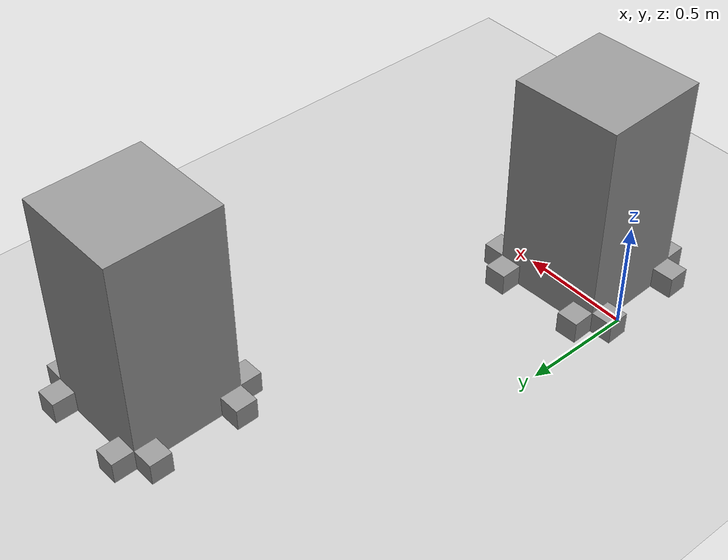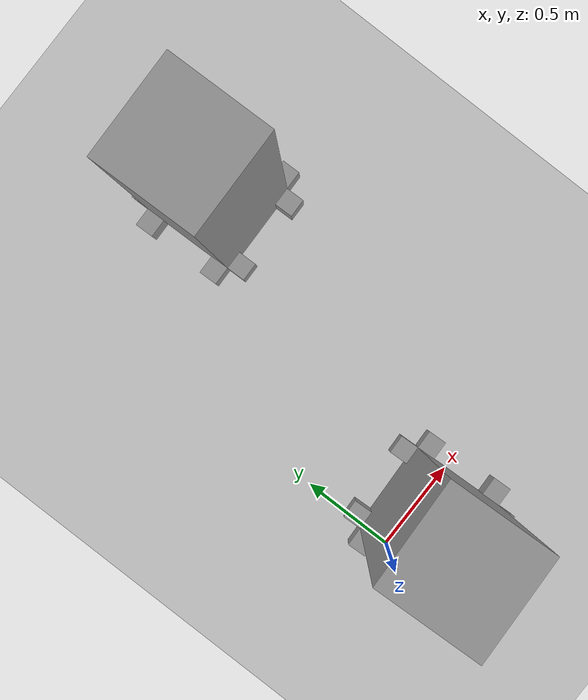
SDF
<sdf version="1.6">
 <world name="default">
  <light name="sun" type="directional">
   <pose>0 0 10 0 -0 0</pose>
   <diffuse>0.8 0.8 0.8 1</diffuse>
   <specular>0.2 0.2 0.2 1</specular>
   <attenuation>
    <range>1000</range>
    <constant>0.9</constant>
    <linear>0.01</linear>
    <quadratic>0.001</quadratic>
   </attenuation>
   <direction>-0.5 0.1 -0.9</direction>
  </light>
  <model name="ground_plane">
   <static>1</static>
   <link name="link">
    <collision name="collision">
     <geometry><plane><normal>0 0 1</normal><size>100 100</size></plane></geometry>
     <surface><friction><ode><mu>100</mu><mu2>50</mu2></ode></friction></surface>
    </collision>
    <visual name="visual">
     <cast_shadows>0</cast_shadows>
     <geometry><plane><normal>0 0 1</normal><size>100 100</size></plane></geometry>
     <material>
      <script><uri>file://media/materials/scripts/gazebo.material</uri><name>Gazebo/Grey</name></script>
     </material>
    </visual>
   </link>
  </model>
  <gravity>0 0 -9.8</gravity>
  <magnetic_field>6e-06 2.3e-05 -4.2e-05</magnetic_field>
  <atmosphere type="adiabatic"/>
  <physics name="default_physics" default="0" type="ode">
   <max_step_size>0.001</max_step_size>
   <real_time_factor>1</real_time_factor>
   <real_time_update_rate>1000</real_time_update_rate>
  </physics>
  <scene><ambient>0.4 0.4 0.4 1</ambient><background>0.7 0.7 0.7 1</background><shadows>1</shadows></scene>
  <spherical_coordinates>
   <surface_model>EARTH_WGS84</surface_model>
   <latitude_deg>0</latitude_deg>
   <longitude_deg>0</longitude_deg>
   <elevation>0</elevation>
   <heading_deg>0</heading_deg>
  </spherical_coordinates>
  <model name="RSS">
   <link name="link_0">
    <inertial>
     <mass>1</mass>
     <inertia>
      <ixx>0.166667</ixx>
      <ixy>0</ixy>
      <ixz>0</ixz>
      <iyy>0.166667</iyy>
      <iyz>0</iyz>
      <izz>0.166667</izz>
     </inertia>
    </inertial>
    <pose>1e-06 -0 0.4 0 -0 0</pose>
    <self_collide>1</self_collide>
    <visual name="visual">
     <pose>0 0 0.1 0 -0 0</pose>
     <geometry><box><size>0.5 0.5 1</size></box></geometry>
     <material>
      <lighting>1</lighting>
      <script><uri>file://media/materials/scripts/gazebo.material</uri><name>Gazebo/Grey</name></script>
      <shader type="pixel"><normal_map>__default__</normal_map></shader>
      <ambient>0.3 0.3 0.3 1</ambient>
      <diffuse>0.7 0.7 0.7 1</diffuse>
      <specular>0.01 0.01 0.01 1</specular>
      <emissive>0 0 0 1</emissive>
     </material>
    </visual>
    <collision name="collision">
     <pose>0 0 0.1 0 -0 0</pose>
     <geometry><box><size>0.5 0.5 1</size></box></geometry>
     <surface>
      <friction>
       <ode><mu>0</mu><mu2>0</mu2><fdir1>0 0 0</fdir1><slip1>0</slip1><slip2>0</slip2></ode>
       <torsional>
        <coefficient>0.98</coefficient>
        <patch_radius>0</patch_radius>
        <surface_radius>0</surface_radius>
        <use_patch_radius>1</use_patch_radius>
        <ode><slip>0</slip></ode>
       </torsional>
      </friction>
      <bounce><restitution_coefficient>0</restitution_coefficient><threshold>1e+06</threshold></bounce>
      <contact>
       <collide_without_contact>0</collide_without_contact>
       <collide_without_contact_bitmask>1</collide_without_contact_bitmask>
       <collide_bitmask>1</collide_bitmask>
       <ode>
        <soft_cfm>0</soft_cfm>
        <soft_erp>0.2</soft_erp>
        <kp>1e+13</kp>
        <kd>1</kd>
        <max_vel>0.01</max_vel>
        <min_depth>0</min_depth>
       </ode>
       <bullet>
        <split_impulse>1</split_impulse>
        <split_impulse_penetration_threshold>-0.01</split_impulse_penetration_threshold>
        <soft_cfm>0</soft_cfm>
        <soft_erp>0.2</soft_erp>
        <kp>1e+13</kp>
        <kd>1</kd>
       </bullet>
      </contact>
     </surface>
    </collision>
   </link>
   <link name="link_0_0">
    <inertial>
     <mass>1</mass>
     <inertia><ixx>0.1</ixx><ixy>0</ixy><ixz>0</ixz><iyy>0.1</iyy><iyz>0</iyz><izz>0.1</izz></inertia>
    </inertial>
    <pose>-0.150008 -0.150038 0.05 -0 -1e-06 9.3e-05</pose>
    <visual name="visual">
     <geometry><sphere><radius>0.1</radius></sphere></geometry>
     <material>
      <lighting>1</lighting>
      <script><uri>file://media/materials/scripts/gazebo.material</uri><name>Gazebo/Grey</name></script>
      <shader type="pixel"><normal_map>__default__</normal_map></shader>
      <ambient>0.3 0.3 0.3 1</ambient>
      <diffuse>0.7 0.7 0.7 1</diffuse>
      <specular>0.01 0.01 0.01 1</specular>
      <emissive>0 0 0 1</emissive>
     </material>
    </visual>
    <collision name="collision">
     <geometry><sphere><radius>0.1</radius></sphere></geometry>
     <surface>
      <friction>
       <ode><mu>1</mu><mu2>1</mu2><fdir1>0 0 0</fdir1><slip1>0</slip1><slip2>0</slip2></ode>
       <torsional>
        <coefficient>1</coefficient>
        <patch_radius>0</patch_radius>
        <surface_radius>0</surface_radius>
        <use_patch_radius>1</use_patch_radius>
        <ode><slip>0</slip></ode>
       </torsional>
      </friction>
      <bounce><restitution_coefficient>0</restitution_coefficient><threshold>1e+06</threshold></bounce>
      <contact>
       <collide_without_contact>0</collide_without_contact>
       <collide_without_contact_bitmask>1</collide_without_contact_bitmask>
       <collide_bitmask>1</collide_bitmask>
       <ode>
        <soft_cfm>0</soft_cfm>
        <soft_erp>0.2</soft_erp>
        <kp>1e+13</kp>
        <kd>1</kd>
        <max_vel>0.01</max_vel>
        <min_depth>0</min_depth>
       </ode>
       <bullet>
        <split_impulse>1</split_impulse>
        <split_impulse_penetration_threshold>-0.01</split_impulse_penetration_threshold>
        <soft_cfm>0</soft_cfm>
        <soft_erp>0.2</soft_erp>
        <kp>1e+13</kp>
        <kd>1</kd>
       </bullet>
      </contact>
     </surface>
    </collision>
   </link>
   <link name="link_0_0_clone">
    <inertial>
     <mass>1</mass>
     <inertia><ixx>0.1</ixx><ixy>0</ixy><ixz>0</ixz><iyy>0.1</iyy><iyz>0</iyz><izz>0.1</izz></inertia>
    </inertial>
    <pose>-0.150027 0.15 0.05 -0 -2e-06 0.000186</pose>
    <visual name="visual_0">
     <geometry><sphere><radius>0.1</radius></sphere></geometry>
     <material>
      <lighting>1</lighting>
      <script><uri>file://media/materials/scripts/gazebo.material</uri><name>Gazebo/Grey</name></script>
      <shader type="pixel"><normal_map>__default__</normal_map></shader>
      <ambient>0.3 0.3 0.3 1</ambient>
      <diffuse>0.7 0.7 0.7 1</diffuse>
      <specular>0.01 0.01 0.01 1</specular>
      <emissive>0 0 0 1</emissive>
     </material>
    </visual>
    <collision name="collision">
     <geometry><sphere><radius>0.1</radius></sphere></geometry>
     <surface>
      <friction>
       <ode><mu>1</mu><mu2>1</mu2><fdir1>0 0 0</fdir1><slip1>0</slip1><slip2>0</slip2></ode>
       <torsional>
        <coefficient>1</coefficient>
        <patch_radius>0</patch_radius>
        <surface_radius>0</surface_radius>
        <use_patch_radius>1</use_patch_radius>
        <ode><slip>0</slip></ode>
       </torsional>
      </friction>
      <bounce><restitution_coefficient>0</restitution_coefficient><threshold>1e+06</threshold></bounce>
      <contact>
       <collide_without_contact>0</collide_without_contact>
       <collide_without_contact_bitmask>1</collide_without_contact_bitmask>
       <collide_bitmask>1</collide_bitmask>
       <ode>
        <soft_cfm>0</soft_cfm>
        <soft_erp>0.2</soft_erp>
        <kp>1e+13</kp>
        <kd>1</kd>
        <max_vel>0.01</max_vel>
        <min_depth>0</min_depth>
       </ode>
       <bullet>
        <split_impulse>1</split_impulse>
        <split_impulse_penetration_threshold>-0.01</split_impulse_penetration_threshold>
        <soft_cfm>0</soft_cfm>
        <soft_erp>0.2</soft_erp>
        <kp>1e+13</kp>
        <kd>1</kd>
       </bullet>
      </contact>
     </surface>
    </collision>
   </link>
   <link name="link_0_0_clone_0">
    <inertial>
     <mass>1</mass>
     <inertia><ixx>0.1</ixx><ixy>0</ixy><ixz>0</ixz><iyy>0.1</iyy><iyz>0</iyz><izz>0.1</izz></inertia>
    </inertial>
    <pose>0.15003 -0.15 0.05 -0 -2e-06 0.000186</pose>
    <visual name="visual_0">
     <geometry><sphere><radius>0.1</radius></sphere></geometry>
     <material>
      <lighting>1</lighting>
      <script><uri>file://media/materials/scripts/gazebo.material</uri><name>Gazebo/Grey</name></script>
      <shader type="pixel"><normal_map>__default__</normal_map></shader>
      <ambient>0.3 0.3 0.3 1</ambient>
      <diffuse>0.7 0.7 0.7 1</diffuse>
      <specular>0.01 0.01 0.01 1</specular>
      <emissive>0 0 0 1</emissive>
     </material>
    </visual>
    <collision name="collision">
     <geometry><sphere><radius>0.1</radius></sphere></geometry>
     <surface>
      <friction>
       <ode><mu>1</mu><mu2>1</mu2><fdir1>0 0 0</fdir1><slip1>0</slip1><slip2>0</slip2></ode>
       <torsional>
        <coefficient>1</coefficient>
        <patch_radius>0</patch_radius>
        <surface_radius>0</surface_radius>
        <use_patch_radius>1</use_patch_radius>
        <ode><slip>0</slip></ode>
       </torsional>
      </friction>
      <bounce><restitution_coefficient>0</restitution_coefficient><threshold>1e+06</threshold></bounce>
      <contact>
       <collide_without_contact>0</collide_without_contact>
       <collide_without_contact_bitmask>1</collide_without_contact_bitmask>
       <collide_bitmask>1</collide_bitmask>
       <ode>
        <soft_cfm>0</soft_cfm>
        <soft_erp>0.2</soft_erp>
        <kp>1e+13</kp>
        <kd>1</kd>
        <max_vel>0.01</max_vel>
        <min_depth>0</min_depth>
       </ode>
       <bullet>
        <split_impulse>1</split_impulse>
        <split_impulse_penetration_threshold>-0.01</split_impulse_penetration_threshold>
        <soft_cfm>0</soft_cfm>
        <soft_erp>0.2</soft_erp>
        <kp>1e+13</kp>
        <kd>1</kd>
       </bullet>
      </contact>
     </surface>
    </collision>
   </link>
   <link name="link_0_0_clone_1">
    <inertial>
     <mass>1</mass>
     <inertia><ixx>0.1</ixx><ixy>0</ixy><ixz>0</ixz><iyy>0.1</iyy><iyz>0</iyz><izz>0.1</izz></inertia>
    </inertial>
    <pose>0.150002 0.150028 0.05 -0 -2e-06 0.000186</pose>
    <visual name="visual_0">
     <geometry><sphere><radius>0.1</radius></sphere></geometry>
     <material>
      <lighting>1</lighting>
      <script><uri>file://media/materials/scripts/gazebo.material</uri><name>Gazebo/Grey</name></script>
      <shader type="pixel"><normal_map>__default__</normal_map></shader>
      <ambient>0.3 0.3 0.3 1</ambient>
      <diffuse>0.7 0.7 0.7 1</diffuse>
      <specular>0.01 0.01 0.01 1</specular>
      <emissive>0 0 0 1</emissive>
     </material>
    </visual>
    <collision name="collision">
     <geometry><sphere><radius>0.1</radius></sphere></geometry>
     <surface>
      <friction>
       <ode><mu>1</mu><mu2>1</mu2><fdir1>0 0 0</fdir1><slip1>0</slip1><slip2>0</slip2></ode>
       <torsional>
        <coefficient>1</coefficient>
        <patch_radius>0</patch_radius>
        <surface_radius>0</surface_radius>
        <use_patch_radius>1</use_patch_radius>
        <ode><slip>0</slip></ode>
       </torsional>
      </friction>
      <bounce><restitution_coefficient>0</restitution_coefficient><threshold>1e+06</threshold></bounce>
      <contact>
       <collide_without_contact>0</collide_without_contact>
       <collide_without_contact_bitmask>1</collide_without_contact_bitmask>
       <collide_bitmask>1</collide_bitmask>
       <ode>
        <soft_cfm>0</soft_cfm>
        <soft_erp>0.2</soft_erp>
        <kp>1e+13</kp>
        <kd>1</kd>
        <max_vel>0.01</max_vel>
        <min_depth>0</min_depth>
       </ode>
       <bullet>
        <split_impulse>1</split_impulse>
        <split_impulse_penetration_threshold>-0.01</split_impulse_penetration_threshold>
        <soft_cfm>0</soft_cfm>
        <soft_erp>0.2</soft_erp>
        <kp>1e+13</kp>
        <kd>1</kd>
       </bullet>
      </contact>
     </surface>
    </collision>
   </link>
   <link name="link_1">
    <inertial>
     <mass>1</mass>
     <inertia>
      <ixx>0.166667</ixx>
      <ixy>0</ixy>
      <ixz>0</ixz>
      <iyy>0.166667</iyy>
      <iyz>0</iyz>
      <izz>0.166667</izz>
     </inertia>
    </inertial>
    <pose>-0.199999 0.299999 -0.05 0 -0 0</pose>
    <self_collide>1</self_collide>
    <visual name="visual">
     <pose>0 0 0.1 0 -0 0</pose>
     <geometry><box><size>0.1 0.1 0.1</size></box></geometry>
     <material>
      <lighting>1</lighting>
      <script><uri>file://media/materials/scripts/gazebo.material</uri><name>Gazebo/Grey</name></script>
      <shader type="pixel"><normal_map>__default__</normal_map></shader>
      <ambient>0.3 0.3 0.3 1</ambient>
      <diffuse>0.7 0.7 0.7 1</diffuse>
      <specular>0.01 0.01 0.01 1</specular>
      <emissive>0 0 0 1</emissive>
     </material>
    </visual>
    <collision name="collision">
     <pose>0 0 0.1 0 -0 0</pose>
     <geometry><box><size>0.1 0.1 0.1</size></box></geometry>
     <surface>
      <friction>
       <ode><mu>0</mu><mu2>1</mu2><fdir1>0 0 0</fdir1><slip1>0</slip1><slip2>0</slip2></ode>
       <torsional>
        <coefficient>1</coefficient>
        <patch_radius>0</patch_radius>
        <surface_radius>0</surface_radius>
        <use_patch_radius>1</use_patch_radius>
        <ode><slip>0</slip></ode>
       </torsional>
      </friction>
      <bounce><restitution_coefficient>0</restitution_coefficient><threshold>1e+06</threshold></bounce>
      <contact>
       <collide_without_contact>0</collide_without_contact>
       <collide_without_contact_bitmask>1</collide_without_contact_bitmask>
       <collide_bitmask>1</collide_bitmask>
       <ode>
        <soft_cfm>0</soft_cfm>
        <soft_erp>0.2</soft_erp>
        <kp>1e+13</kp>
        <kd>1</kd>
        <max_vel>0.01</max_vel>
        <min_depth>0</min_depth>
       </ode>
       <bullet>
        <split_impulse>1</split_impulse>
        <split_impulse_penetration_threshold>-0.01</split_impulse_penetration_threshold>
        <soft_cfm>0</soft_cfm>
        <soft_erp>0.2</soft_erp>
        <kp>1e+13</kp>
        <kd>1</kd>
       </bullet>
      </contact>
     </surface>
    </collision>
   </link>
   <link name="link_1_clone">
    <inertial>
     <mass>1</mass>
     <inertia>
      <ixx>0.166667</ixx>
      <ixy>0</ixy>
      <ixz>0</ixz>
      <iyy>0.166667</iyy>
      <iyz>0</iyz>
      <izz>0.166667</izz>
     </inertia>
    </inertial>
    <pose>0.199999 0.3 -0.05 0 -0 0</pose>
    <self_collide>1</self_collide>
    <visual name="visual">
     <pose>0 0 0.1 0 -0 0</pose>
     <geometry><box><size>0.1 0.1 0.1</size></box></geometry>
     <material>
      <lighting>1</lighting>
      <script><uri>file://media/materials/scripts/gazebo.material</uri><name>Gazebo/Grey</name></script>
      <shader type="pixel"><normal_map>__default__</normal_map></shader>
      <ambient>0.3 0.3 0.3 1</ambient>
      <diffuse>0.7 0.7 0.7 1</diffuse>
      <specular>0.01 0.01 0.01 1</specular>
      <emissive>0 0 0 1</emissive>
     </material>
    </visual>
    <collision name="collision">
     <pose>0 0 0.1 0 -0 0</pose>
     <geometry><box><size>0.1 0.1 0.1</size></box></geometry>
     <surface>
      <friction>
       <ode><mu>0</mu><mu2>0</mu2><fdir1>0 0 0</fdir1><slip1>0</slip1><slip2>0</slip2></ode>
       <torsional>
        <coefficient>1</coefficient>
        <patch_radius>0</patch_radius>
        <surface_radius>0</surface_radius>
        <use_patch_radius>1</use_patch_radius>
        <ode><slip>0</slip></ode>
       </torsional>
      </friction>
      <bounce><restitution_coefficient>0</restitution_coefficient><threshold>1e+06</threshold></bounce>
      <contact>
       <collide_without_contact>0</collide_without_contact>
       <collide_without_contact_bitmask>1</collide_without_contact_bitmask>
       <collide_bitmask>1</collide_bitmask>
       <ode>
        <soft_cfm>0</soft_cfm>
        <soft_erp>0.2</soft_erp>
        <kp>1e+13</kp>
        <kd>1</kd>
        <max_vel>0.01</max_vel>
        <min_depth>0</min_depth>
       </ode>
       <bullet>
        <split_impulse>1</split_impulse>
        <split_impulse_penetration_threshold>-0.01</split_impulse_penetration_threshold>
        <soft_cfm>0</soft_cfm>
        <soft_erp>0.2</soft_erp>
        <kp>1e+13</kp>
        <kd>1</kd>
       </bullet>
      </contact>
     </surface>
    </collision>
   </link>
   <link name="link_1_clone_0">
    <inertial>
     <mass>1</mass>
     <inertia>
      <ixx>0.166667</ixx>
      <ixy>0</ixy>
      <ixz>0</ixz>
      <iyy>0.166667</iyy>
      <iyz>0</iyz>
      <izz>0.166667</izz>
     </inertia>
    </inertial>
    <pose>-0.299999 0.2 -0.05 0 -0 0</pose>
    <self_collide>1</self_collide>
    <visual name="visual">
     <pose>0 0 0.1 0 -0 0</pose>
     <geometry><box><size>0.1 0.1 0.1</size></box></geometry>
     <material>
      <lighting>1</lighting>
      <script><uri>file://media/materials/scripts/gazebo.material</uri><name>Gazebo/Grey</name></script>
      <shader type="pixel"><normal_map>__default__</normal_map></shader>
      <ambient>0.3 0.3 0.3 1</ambient>
      <diffuse>0.7 0.7 0.7 1</diffuse>
      <specular>0.01 0.01 0.01 1</specular>
      <emissive>0 0 0 1</emissive>
     </material>
    </visual>
    <collision name="collision">
     <pose>0 0 0.1 0 -0 0</pose>
     <geometry><box><size>0.1 0.1 0.1</size></box></geometry>
     <surface>
      <friction>
       <ode><mu>0</mu><mu2>0</mu2><fdir1>0 0 0</fdir1><slip1>0</slip1><slip2>0</slip2></ode>
       <torsional>
        <coefficient>1</coefficient>
        <patch_radius>0</patch_radius>
        <surface_radius>0</surface_radius>
        <use_patch_radius>1</use_patch_radius>
        <ode><slip>0</slip></ode>
       </torsional>
      </friction>
      <bounce><restitution_coefficient>0</restitution_coefficient><threshold>1e+06</threshold></bounce>
      <contact>
       <collide_without_contact>0</collide_without_contact>
       <collide_without_contact_bitmask>1</collide_without_contact_bitmask>
       <collide_bitmask>1</collide_bitmask>
       <ode>
        <soft_cfm>0</soft_cfm>
        <soft_erp>0.2</soft_erp>
        <kp>1e+13</kp>
        <kd>1</kd>
        <max_vel>0.01</max_vel>
        <min_depth>0</min_depth>
       </ode>
       <bullet>
        <split_impulse>1</split_impulse>
        <split_impulse_penetration_threshold>-0.01</split_impulse_penetration_threshold>
        <soft_cfm>0</soft_cfm>
        <soft_erp>0.2</soft_erp>
        <kp>1e+13</kp>
        <kd>1</kd>
       </bullet>
      </contact>
     </surface>
    </collision>
   </link>
   <link name="link_1_clone_1">
    <inertial>
     <mass>1</mass>
     <inertia>
      <ixx>0.166667</ixx>
      <ixy>0</ixy>
      <ixz>0</ixz>
      <iyy>0.166667</iyy>
      <iyz>0</iyz>
      <izz>0.166667</izz>
     </inertia>
    </inertial>
    <pose>-0.299999 -0.2 -0.05 0 -0 0</pose>
    <self_collide>1</self_collide>
    <visual name="visual">
     <pose>0 0 0.1 0 -0 0</pose>
     <geometry><box><size>0.1 0.1 0.1</size></box></geometry>
     <material>
      <lighting>1</lighting>
      <script><uri>file://media/materials/scripts/gazebo.material</uri><name>Gazebo/Grey</name></script>
      <shader type="pixel"><normal_map>__default__</normal_map></shader>
      <ambient>0.3 0.3 0.3 1</ambient>
      <diffuse>0.7 0.7 0.7 1</diffuse>
      <specular>0.01 0.01 0.01 1</specular>
      <emissive>0 0 0 1</emissive>
     </material>
    </visual>
    <collision name="collision">
     <pose>0 0 0.1 0 -0 0</pose>
     <geometry><box><size>0.1 0.1 0.1</size></box></geometry>
     <surface>
      <friction>
       <ode><mu>0</mu><mu2>0</mu2><fdir1>0 0 0</fdir1><slip1>0</slip1><slip2>0</slip2></ode>
       <torsional>
        <coefficient>1</coefficient>
        <patch_radius>0</patch_radius>
        <surface_radius>0</surface_radius>
        <use_patch_radius>1</use_patch_radius>
        <ode><slip>0</slip></ode>
       </torsional>
      </friction>
      <bounce><restitution_coefficient>0</restitution_coefficient><threshold>1e+06</threshold></bounce>
      <contact>
       <collide_without_contact>0</collide_without_contact>
       <collide_without_contact_bitmask>1</collide_without_contact_bitmask>
       <collide_bitmask>1</collide_bitmask>
       <ode>
        <soft_cfm>0</soft_cfm>
        <soft_erp>0.2</soft_erp>
        <kp>1e+13</kp>
        <kd>1</kd>
        <max_vel>0.01</max_vel>
        <min_depth>0</min_depth>
       </ode>
       <bullet>
        <split_impulse>1</split_impulse>
        <split_impulse_penetration_threshold>-0.01</split_impulse_penetration_threshold>
        <soft_cfm>0</soft_cfm>
        <soft_erp>0.2</soft_erp>
        <kp>1e+13</kp>
        <kd>1</kd>
       </bullet>
      </contact>
     </surface>
    </collision>
   </link>
   <link name="link_1_clone_2">
    <inertial>
     <mass>1</mass>
     <inertia>
      <ixx>0.166667</ixx>
      <ixy>0</ixy>
      <ixz>0</ixz>
      <iyy>0.166667</iyy>
      <iyz>0</iyz>
      <izz>0.166667</izz>
     </inertia>
    </inertial>
    <pose>0.2 -0.3 -0.05 0 -0 0</pose>
    <self_collide>1</self_collide>
    <visual name="visual">
     <pose>0 0 0.1 0 -0 0</pose>
     <geometry><box><size>0.1 0.1 0.1</size></box></geometry>
     <material>
      <lighting>1</lighting>
      <script><uri>file://media/materials/scripts/gazebo.material</uri><name>Gazebo/Grey</name></script>
      <shader type="pixel"><normal_map>__default__</normal_map></shader>
      <ambient>0.3 0.3 0.3 1</ambient>
      <diffuse>0.7 0.7 0.7 1</diffuse>
      <specular>0.01 0.01 0.01 1</specular>
      <emissive>0 0 0 1</emissive>
     </material>
    </visual>
    <collision name="collision">
     <pose>0 0 0.1 0 -0 0</pose>
     <geometry><box><size>0.1 0.1 0.1</size></box></geometry>
     <surface>
      <friction>
       <ode><mu>0</mu><mu2>0</mu2><fdir1>0 0 0</fdir1><slip1>0</slip1><slip2>0</slip2></ode>
       <torsional>
        <coefficient>1</coefficient>
        <patch_radius>0</patch_radius>
        <surface_radius>0</surface_radius>
        <use_patch_radius>1</use_patch_radius>
        <ode><slip>0</slip></ode>
       </torsional>
      </friction>
      <bounce><restitution_coefficient>0</restitution_coefficient><threshold>1e+06</threshold></bounce>
      <contact>
       <collide_without_contact>0</collide_without_contact>
       <collide_without_contact_bitmask>1</collide_without_contact_bitmask>
       <collide_bitmask>1</collide_bitmask>
       <ode>
        <soft_cfm>0</soft_cfm>
        <soft_erp>0.2</soft_erp>
        <kp>1e+13</kp>
        <kd>1</kd>
        <max_vel>0.01</max_vel>
        <min_depth>0</min_depth>
       </ode>
       <bullet>
        <split_impulse>1</split_impulse>
        <split_impulse_penetration_threshold>-0.01</split_impulse_penetration_threshold>
        <soft_cfm>0</soft_cfm>
        <soft_erp>0.2</soft_erp>
        <kp>1e+13</kp>
        <kd>1</kd>
       </bullet>
      </contact>
     </surface>
    </collision>
   </link>
   <link name="link_1_clone_3">
    <inertial>
     <mass>1</mass>
     <inertia>
      <ixx>0.166667</ixx>
      <ixy>0</ixy>
      <ixz>0</ixz>
      <iyy>0.166667</iyy>
      <iyz>0</iyz>
      <izz>0.166667</izz>
     </inertia>
    </inertial>
    <pose>-0.2 -0.3 -0.05 0 -0 0</pose>
    <self_collide>1</self_collide>
    <visual name="visual">
     <pose>0 0 0.1 0 -0 0</pose>
     <geometry><box><size>0.1 0.1 0.1</size></box></geometry>
     <material>
      <lighting>1</lighting>
      <script><uri>file://media/materials/scripts/gazebo.material</uri><name>Gazebo/Grey</name></script>
      <shader type="pixel"><normal_map>__default__</normal_map></shader>
      <ambient>0.3 0.3 0.3 1</ambient>
      <diffuse>0.7 0.7 0.7 1</diffuse>
      <specular>0.01 0.01 0.01 1</specular>
      <emissive>0 0 0 1</emissive>
     </material>
    </visual>
    <collision name="collision">
     <pose>0 0 0.1 0 -0 0</pose>
     <geometry><box><size>0.1 0.1 0.1</size></box></geometry>
     <surface>
      <friction>
       <ode><mu>0</mu><mu2>0</mu2><fdir1>0 0 0</fdir1><slip1>0</slip1><slip2>0</slip2></ode>
       <torsional>
        <coefficient>1</coefficient>
        <patch_radius>0</patch_radius>
        <surface_radius>0</surface_radius>
        <use_patch_radius>1</use_patch_radius>
        <ode><slip>0</slip></ode>
       </torsional>
      </friction>
      <bounce><restitution_coefficient>0</restitution_coefficient><threshold>1e+06</threshold></bounce>
      <contact>
       <collide_without_contact>0</collide_without_contact>
       <collide_without_contact_bitmask>1</collide_without_contact_bitmask>
       <collide_bitmask>1</collide_bitmask>
       <ode>
        <soft_cfm>0</soft_cfm>
        <soft_erp>0.2</soft_erp>
        <kp>1e+13</kp>
        <kd>1</kd>
        <max_vel>0.01</max_vel>
        <min_depth>0</min_depth>
       </ode>
       <bullet>
        <split_impulse>1</split_impulse>
        <split_impulse_penetration_threshold>-0.01</split_impulse_penetration_threshold>
        <soft_cfm>0</soft_cfm>
        <soft_erp>0.2</soft_erp>
        <kp>1e+13</kp>
        <kd>1</kd>
       </bullet>
      </contact>
     </surface>
    </collision>
   </link>
   <link name="link_1_clone_4">
    <inertial>
     <mass>1</mass>
     <inertia>
      <ixx>0.166667</ixx>
      <ixy>0</ixy>
      <ixz>0</ixz>
      <iyy>0.166667</iyy>
      <iyz>0</iyz>
      <izz>0.166667</izz>
     </inertia>
    </inertial>
    <pose>0.3 -0.200001 -0.05 0 -0 0</pose>
    <self_collide>1</self_collide>
    <visual name="visual">
     <pose>0 0 0.1 0 -0 0</pose>
     <geometry><box><size>0.1 0.1 0.1</size></box></geometry>
     <material>
      <lighting>1</lighting>
      <script><uri>file://media/materials/scripts/gazebo.material</uri><name>Gazebo/Grey</name></script>
      <shader type="pixel"><normal_map>__default__</normal_map></shader>
      <ambient>0.3 0.3 0.3 1</ambient>
      <diffuse>0.7 0.7 0.7 1</diffuse>
      <specular>0.01 0.01 0.01 1</specular>
      <emissive>0 0 0 1</emissive>
     </material>
    </visual>
    <collision name="collision">
     <pose>0 0 0.1 0 -0 0</pose>
     <geometry><box><size>0.1 0.1 0.1</size></box></geometry>
     <surface>
      <friction>
       <ode><mu>0</mu><mu2>0</mu2><fdir1>0 0 0</fdir1><slip1>0</slip1><slip2>0</slip2></ode>
       <torsional>
        <coefficient>1</coefficient>
        <patch_radius>0</patch_radius>
        <surface_radius>0</surface_radius>
        <use_patch_radius>1</use_patch_radius>
        <ode><slip>0</slip></ode>
       </torsional>
      </friction>
      <bounce><restitution_coefficient>0</restitution_coefficient><threshold>1e+06</threshold></bounce>
      <contact>
       <collide_without_contact>0</collide_without_contact>
       <collide_without_contact_bitmask>1</collide_without_contact_bitmask>
       <collide_bitmask>1</collide_bitmask>
       <ode>
        <soft_cfm>0</soft_cfm>
        <soft_erp>0.2</soft_erp>
        <kp>1e+13</kp>
        <kd>1</kd>
        <max_vel>0.01</max_vel>
        <min_depth>0</min_depth>
       </ode>
       <bullet>
        <split_impulse>1</split_impulse>
        <split_impulse_penetration_threshold>-0.01</split_impulse_penetration_threshold>
        <soft_cfm>0</soft_cfm>
        <soft_erp>0.2</soft_erp>
        <kp>1e+13</kp>
        <kd>1</kd>
       </bullet>
      </contact>
     </surface>
    </collision>
   </link>
   <link name="link_1_clone_5">
    <inertial>
     <mass>1</mass>
     <inertia>
      <ixx>0.166667</ixx>
      <ixy>0</ixy>
      <ixz>0</ixz>
      <iyy>0.166667</iyy>
      <iyz>0</iyz>
      <izz>0.166667</izz>
     </inertia>
    </inertial>
    <pose>0.3 0.199999 -0.05 0 -0 0</pose>
    <self_collide>1</self_collide>
    <visual name="visual">
     <pose>0 0 0.1 0 -0 0</pose>
     <geometry><box><size>0.1 0.1 0.1</size></box></geometry>
     <material>
      <lighting>1</lighting>
      <script><uri>file://media/materials/scripts/gazebo.material</uri><name>Gazebo/Grey</name></script>
      <shader type="pixel"><normal_map>__default__</normal_map></shader>
      <ambient>0.3 0.3 0.3 1</ambient>
      <diffuse>0.7 0.7 0.7 1</diffuse>
      <specular>0.01 0.01 0.01 1</specular>
      <emissive>0 0 0 1</emissive>
     </material>
    </visual>
    <collision name="collision">
     <pose>0 0 0.1 0 -0 0</pose>
     <geometry><box><size>0.1 0.1 0.1</size></box></geometry>
     <surface>
      <friction>
       <ode><mu>0</mu><mu2>0</mu2><fdir1>0 0 0</fdir1><slip1>0</slip1><slip2>0</slip2></ode>
       <torsional>
        <coefficient>1</coefficient>
        <patch_radius>0</patch_radius>
        <surface_radius>0</surface_radius>
        <use_patch_radius>1</use_patch_radius>
        <ode><slip>0</slip></ode>
       </torsional>
      </friction>
      <bounce><restitution_coefficient>0</restitution_coefficient><threshold>1e+06</threshold></bounce>
      <contact>
       <collide_without_contact>0</collide_without_contact>
       <collide_without_contact_bitmask>1</collide_without_contact_bitmask>
       <collide_bitmask>1</collide_bitmask>
       <ode>
        <soft_cfm>0</soft_cfm>
        <soft_erp>0.2</soft_erp>
        <kp>1e+13</kp>
        <kd>1</kd>
        <max_vel>0.01</max_vel>
        <min_depth>0</min_depth>
       </ode>
       <bullet>
        <split_impulse>1</split_impulse>
        <split_impulse_penetration_threshold>-0.01</split_impulse_penetration_threshold>
        <soft_cfm>0</soft_cfm>
        <soft_erp>0.2</soft_erp>
        <kp>1e+13</kp>
        <kd>1</kd>
       </bullet>
      </contact>
     </surface>
    </collision>
   </link>
   <joint name="link_0_JOINT_0_0" type="revolute">
    <parent>link_0</parent>
    <child>link_0_0</child>
    <axis>
     <xyz>1 0 0</xyz>
     <use_parent_model_frame>0</use_parent_model_frame>
     <limit>
      <lower>-1.79769e+308</lower>
      <upper>1.79769e+308</upper>
      <effort>-1</effort>
      <velocity>-1</velocity>
     </limit>
     <dynamics>
      <spring_reference>0</spring_reference>
      <spring_stiffness>0</spring_stiffness>
      <damping>0</damping>
      <friction>0</friction>
     </dynamics>
    </axis>
    <physics>
     <ode><limit><cfm>0</cfm><erp>0.2</erp></limit><suspension><cfm>0</cfm><erp>0.2</erp></suspension></ode>
    </physics>
   </joint>
   <joint name="link_0_JOINT_0" type="fixed">
    <parent>link_0</parent>
    <child>link_1</child>
    <physics>
     <ode><limit><cfm>0</cfm><erp>0.2</erp></limit><suspension><cfm>0</cfm><erp>0.2</erp></suspension></ode>
    </physics>
   </joint>
   <joint name="link_0_JOINT_1_0" type="revolute">
    <parent>link_0</parent>
    <child>link_0_0_clone</child>
    <axis>
     <xyz>1 0 0</xyz>
     <use_parent_model_frame>0</use_parent_model_frame>
     <limit>
      <lower>-1.79769e+308</lower>
      <upper>1.79769e+308</upper>
      <effort>-1</effort>
      <velocity>-1</velocity>
     </limit>
     <dynamics>
      <spring_reference>0</spring_reference>
      <spring_stiffness>0</spring_stiffness>
      <damping>0</damping>
      <friction>0</friction>
     </dynamics>
    </axis>
    <physics>
     <ode><limit><cfm>0</cfm><erp>0.2</erp></limit><suspension><cfm>0</cfm><erp>0.2</erp></suspension></ode>
    </physics>
   </joint>
   <joint name="link_0_JOINT_1" type="fixed">
    <parent>link_0</parent>
    <child>link_1_clone</child>
    <physics>
     <ode><limit><cfm>0</cfm><erp>0.2</erp></limit><suspension><cfm>0</cfm><erp>0.2</erp></suspension></ode>
    </physics>
   </joint>
   <joint name="link_0_JOINT_2_0" type="revolute">
    <parent>link_0</parent>
    <child>link_0_0_clone_0</child>
    <axis>
     <xyz>1 0 0</xyz>
     <use_parent_model_frame>0</use_parent_model_frame>
     <limit>
      <lower>-1.79769e+308</lower>
      <upper>1.79769e+308</upper>
      <effort>-1</effort>
      <velocity>-1</velocity>
     </limit>
     <dynamics>
      <spring_reference>0</spring_reference>
      <spring_stiffness>0</spring_stiffness>
      <damping>0</damping>
      <friction>0</friction>
     </dynamics>
    </axis>
    <physics>
     <ode><limit><cfm>0</cfm><erp>0.2</erp></limit><suspension><cfm>0</cfm><erp>0.2</erp></suspension></ode>
    </physics>
   </joint>
   <joint name="link_0_JOINT_2" type="fixed">
    <parent>link_0</parent>
    <child>link_1_clone_0</child>
    <physics>
     <ode><limit><cfm>0</cfm><erp>0.2</erp></limit><suspension><cfm>0</cfm><erp>0.2</erp></suspension></ode>
    </physics>
   </joint>
   <joint name="link_0_JOINT_3_0" type="revolute">
    <parent>link_0</parent>
    <child>link_0_0_clone_1</child>
    <axis>
     <xyz>1 0 0</xyz>
     <use_parent_model_frame>0</use_parent_model_frame>
     <limit>
      <lower>-1.79769e+308</lower>
      <upper>1.79769e+308</upper>
      <effort>-1</effort>
      <velocity>-1</velocity>
     </limit>
     <dynamics>
      <spring_reference>0</spring_reference>
      <spring_stiffness>0</spring_stiffness>
      <damping>0</damping>
      <friction>0</friction>
     </dynamics>
    </axis>
    <physics>
     <ode><limit><cfm>0</cfm><erp>0.2</erp></limit><suspension><cfm>0</cfm><erp>0.2</erp></suspension></ode>
    </physics>
   </joint>
   <joint name="link_0_JOINT_3" type="fixed">
    <parent>link_0</parent>
    <child>link_1_clone_1</child>
    <physics>
     <ode><limit><cfm>0</cfm><erp>0.2</erp></limit><suspension><cfm>0</cfm><erp>0.2</erp></suspension></ode>
    </physics>
   </joint>
   <joint name="link_0_JOINT_4" type="fixed">
    <parent>link_0</parent>
    <child>link_1_clone_2</child>
    <physics>
     <ode><limit><cfm>0</cfm><erp>0.2</erp></limit><suspension><cfm>0</cfm><erp>0.2</erp></suspension></ode>
    </physics>
   </joint>
   <joint name="link_0_JOINT_5" type="fixed">
    <parent>link_0</parent>
    <child>link_1_clone_3</child>
    <physics>
     <ode><limit><cfm>0</cfm><erp>0.2</erp></limit><suspension><cfm>0</cfm><erp>0.2</erp></suspension></ode>
    </physics>
   </joint>
   <joint name="link_0_JOINT_6" type="fixed">
    <parent>link_0</parent>
    <child>link_1_clone_4</child>
    <physics>
     <ode><limit><cfm>0</cfm><erp>0.2</erp></limit><suspension><cfm>0</cfm><erp>0.2</erp></suspension></ode>
    </physics>
   </joint>
   <joint name="link_0_JOINT_7" type="fixed">
    <parent>link_0</parent>
    <child>link_1_clone_5</child>
    <physics>
     <ode><limit><cfm>0</cfm><erp>0.2</erp></limit><suspension><cfm>0</cfm><erp>0.2</erp></suspension></ode>
    </physics>
   </joint>
   <static>0</static>
   <plugin name="imu_plugin" filename="libimu_plugin.so"/>
   <plugin name="model_push" filename="libmodel_push.so"/>
   <pose>0.261231 -0.059569 0.050002 1.5e-05 -1.1e-05 -1.52986</pose>
  </model>
  <model name="RSS_Debris">
   <link name="link_0">
    <inertial>
     <mass>0.35</mass>
     <inertia>
      <ixx>0.0364583</ixx>
      <ixy>0</ixy>
      <ixz>0</ixz>
      <iyy>0.0364583</iyy>
      <iyz>0</iyz>
      <izz>0.0145833</izz>
     </inertia>
    </inertial>
    <pose>1e-06 -0 0.4 0 -0 0</pose>
    <self_collide>1</self_collide>
    <visual name="visual">
     <pose>0 0 0.1 0 -0 0</pose>
     <geometry><box><size>0.5 0.5 1</size></box></geometry>
     <material>
      <lighting>1</lighting>
      <script><uri>file://media/materials/scripts/gazebo.material</uri><name>Gazebo/Grey</name></script>
      <shader type="pixel"><normal_map>__default__</normal_map></shader>
      <ambient>0.3 0.3 0.3 1</ambient>
      <diffuse>0.7 0.7 0.7 1</diffuse>
      <specular>0.01 0.01 0.01 1</specular>
      <emissive>0 0 0 1</emissive>
     </material>
    </visual>
    <collision name="collision">
     <pose>0 0 0.1 0 -0 0</pose>
     <geometry><box><size>0.5 0.5 1</size></box></geometry>
     <surface>
      <friction>
       <ode><mu>0</mu><mu2>0</mu2><fdir1>0 0 0</fdir1><slip1>0</slip1><slip2>0</slip2></ode>
       <torsional>
        <coefficient>0.98</coefficient>
        <patch_radius>0</patch_radius>
        <surface_radius>0</surface_radius>
        <use_patch_radius>1</use_patch_radius>
        <ode><slip>0</slip></ode>
       </torsional>
      </friction>
      <bounce><restitution_coefficient>0</restitution_coefficient><threshold>1e+06</threshold></bounce>
      <contact>
       <collide_without_contact>0</collide_without_contact>
       <collide_without_contact_bitmask>1</collide_without_contact_bitmask>
       <collide_bitmask>1</collide_bitmask>
       <ode>
        <soft_cfm>0</soft_cfm>
        <soft_erp>0.2</soft_erp>
        <kp>1e+13</kp>
        <kd>1</kd>
        <max_vel>0.01</max_vel>
        <min_depth>0</min_depth>
       </ode>
       <bullet>
        <split_impulse>1</split_impulse>
        <split_impulse_penetration_threshold>-0.01</split_impulse_penetration_threshold>
        <soft_cfm>0</soft_cfm>
        <soft_erp>0.2</soft_erp>
        <kp>1e+13</kp>
        <kd>1</kd>
       </bullet>
      </contact>
     </surface>
    </collision>
   </link>
   <link name="link_0_0">
    <inertial>
     <mass>0.35</mass>
     <inertia><ixx>0.0014</ixx><ixy>0</ixy><ixz>0</ixz><iyy>0.0014</iyy><iyz>0</iyz><izz>0.0014</izz></inertia>
    </inertial>
    <pose>-0.150008 -0.150038 0.05 -0 -1e-06 9.3e-05</pose>
    <visual name="visual">
     <geometry><sphere><radius>0.1</radius></sphere></geometry>
     <material>
      <lighting>1</lighting>
      <script><uri>file://media/materials/scripts/gazebo.material</uri><name>Gazebo/Grey</name></script>
      <shader type="pixel"><normal_map>__default__</normal_map></shader>
      <ambient>0.3 0.3 0.3 1</ambient>
      <diffuse>0.7 0.7 0.7 1</diffuse>
      <specular>0.01 0.01 0.01 1</specular>
      <emissive>0 0 0 1</emissive>
     </material>
    </visual>
    <collision name="collision">
     <geometry><sphere><radius>0.1</radius></sphere></geometry>
     <surface>
      <friction>
       <ode><mu>1</mu><mu2>1</mu2><fdir1>0 0 0</fdir1><slip1>0</slip1><slip2>0</slip2></ode>
       <torsional>
        <coefficient>1</coefficient>
        <patch_radius>0</patch_radius>
        <surface_radius>0</surface_radius>
        <use_patch_radius>1</use_patch_radius>
        <ode><slip>0</slip></ode>
       </torsional>
      </friction>
      <bounce><restitution_coefficient>0</restitution_coefficient><threshold>1e+06</threshold></bounce>
      <contact>
       <collide_without_contact>0</collide_without_contact>
       <collide_without_contact_bitmask>1</collide_without_contact_bitmask>
       <collide_bitmask>1</collide_bitmask>
       <ode>
        <soft_cfm>0</soft_cfm>
        <soft_erp>0.2</soft_erp>
        <kp>1e+13</kp>
        <kd>1</kd>
        <max_vel>0.01</max_vel>
        <min_depth>0</min_depth>
       </ode>
       <bullet>
        <split_impulse>1</split_impulse>
        <split_impulse_penetration_threshold>-0.01</split_impulse_penetration_threshold>
        <soft_cfm>0</soft_cfm>
        <soft_erp>0.2</soft_erp>
        <kp>1e+13</kp>
        <kd>1</kd>
       </bullet>
      </contact>
     </surface>
    </collision>
   </link>
   <link name="link_0_0_clone">
    <inertial>
     <mass>0.35</mass>
     <inertia><ixx>0.0014</ixx><ixy>0</ixy><ixz>0</ixz><iyy>0.0014</iyy><iyz>0</iyz><izz>0.0014</izz></inertia>
    </inertial>
    <pose>-0.150027 0.15 0.05 -0 -2e-06 0.000186</pose>
    <visual name="visual_0">
     <geometry><sphere><radius>0.1</radius></sphere></geometry>
     <material>
      <lighting>1</lighting>
      <script><uri>file://media/materials/scripts/gazebo.material</uri><name>Gazebo/Grey</name></script>
      <shader type="pixel"><normal_map>__default__</normal_map></shader>
      <ambient>0.3 0.3 0.3 1</ambient>
      <diffuse>0.7 0.7 0.7 1</diffuse>
      <specular>0.01 0.01 0.01 1</specular>
      <emissive>0 0 0 1</emissive>
     </material>
    </visual>
    <collision name="collision">
     <geometry><sphere><radius>0.1</radius></sphere></geometry>
     <surface>
      <friction>
       <ode><mu>1</mu><mu2>1</mu2><fdir1>0 0 0</fdir1><slip1>0</slip1><slip2>0</slip2></ode>
       <torsional>
        <coefficient>1</coefficient>
        <patch_radius>0</patch_radius>
        <surface_radius>0</surface_radius>
        <use_patch_radius>1</use_patch_radius>
        <ode><slip>0</slip></ode>
       </torsional>
      </friction>
      <bounce><restitution_coefficient>0</restitution_coefficient><threshold>1e+06</threshold></bounce>
      <contact>
       <collide_without_contact>0</collide_without_contact>
       <collide_without_contact_bitmask>1</collide_without_contact_bitmask>
       <collide_bitmask>1</collide_bitmask>
       <ode>
        <soft_cfm>0</soft_cfm>
        <soft_erp>0.2</soft_erp>
        <kp>1e+13</kp>
        <kd>1</kd>
        <max_vel>0.01</max_vel>
        <min_depth>0</min_depth>
       </ode>
       <bullet>
        <split_impulse>1</split_impulse>
        <split_impulse_penetration_threshold>-0.01</split_impulse_penetration_threshold>
        <soft_cfm>0</soft_cfm>
        <soft_erp>0.2</soft_erp>
        <kp>1e+13</kp>
        <kd>1</kd>
       </bullet>
      </contact>
     </surface>
    </collision>
   </link>
   <link name="link_0_0_clone_0">
    <inertial>
     <mass>0.35</mass>
     <inertia><ixx>0.0014</ixx><ixy>0</ixy><ixz>0</ixz><iyy>0.0014</iyy><iyz>0</iyz><izz>0.0014</izz></inertia>
    </inertial>
    <pose>0.15003 -0.15 0.05 -0 -2e-06 0.000186</pose>
    <visual name="visual_0">
     <geometry><sphere><radius>0.1</radius></sphere></geometry>
     <material>
      <lighting>1</lighting>
      <script><uri>file://media/materials/scripts/gazebo.material</uri><name>Gazebo/Grey</name></script>
      <shader type="pixel"><normal_map>__default__</normal_map></shader>
      <ambient>0.3 0.3 0.3 1</ambient>
      <diffuse>0.7 0.7 0.7 1</diffuse>
      <specular>0.01 0.01 0.01 1</specular>
      <emissive>0 0 0 1</emissive>
     </material>
    </visual>
    <collision name="collision">
     <geometry><sphere><radius>0.1</radius></sphere></geometry>
     <surface>
      <friction>
       <ode><mu>1</mu><mu2>1</mu2><fdir1>0 0 0</fdir1><slip1>0</slip1><slip2>0</slip2></ode>
       <torsional>
        <coefficient>1</coefficient>
        <patch_radius>0</patch_radius>
        <surface_radius>0</surface_radius>
        <use_patch_radius>1</use_patch_radius>
        <ode><slip>0</slip></ode>
       </torsional>
      </friction>
      <bounce><restitution_coefficient>0</restitution_coefficient><threshold>1e+06</threshold></bounce>
      <contact>
       <collide_without_contact>0</collide_without_contact>
       <collide_without_contact_bitmask>1</collide_without_contact_bitmask>
       <collide_bitmask>1</collide_bitmask>
       <ode>
        <soft_cfm>0</soft_cfm>
        <soft_erp>0.2</soft_erp>
        <kp>1e+13</kp>
        <kd>1</kd>
        <max_vel>0.01</max_vel>
        <min_depth>0</min_depth>
       </ode>
       <bullet>
        <split_impulse>1</split_impulse>
        <split_impulse_penetration_threshold>-0.01</split_impulse_penetration_threshold>
        <soft_cfm>0</soft_cfm>
        <soft_erp>0.2</soft_erp>
        <kp>1e+13</kp>
        <kd>1</kd>
       </bullet>
      </contact>
     </surface>
    </collision>
   </link>
   <link name="link_0_0_clone_1">
    <inertial>
     <mass>0.35</mass>
     <inertia><ixx>0.0014</ixx><ixy>0</ixy><ixz>0</ixz><iyy>0.0014</iyy><iyz>0</iyz><izz>0.0014</izz></inertia>
    </inertial>
    <pose>0.150002 0.150028 0.05 -0 -2e-06 0.000186</pose>
    <visual name="visual_0">
     <geometry><sphere><radius>0.1</radius></sphere></geometry>
     <material>
      <lighting>1</lighting>
      <script><uri>file://media/materials/scripts/gazebo.material</uri><name>Gazebo/Grey</name></script>
      <shader type="pixel"><normal_map>__default__</normal_map></shader>
      <ambient>0.3 0.3 0.3 1</ambient>
      <diffuse>0.7 0.7 0.7 1</diffuse>
      <specular>0.01 0.01 0.01 1</specular>
      <emissive>0 0 0 1</emissive>
     </material>
    </visual>
    <collision name="collision">
     <geometry><sphere><radius>0.1</radius></sphere></geometry>
     <surface>
      <friction>
       <ode><mu>1</mu><mu2>1</mu2><fdir1>0 0 0</fdir1><slip1>0</slip1><slip2>0</slip2></ode>
       <torsional>
        <coefficient>1</coefficient>
        <patch_radius>0</patch_radius>
        <surface_radius>0</surface_radius>
        <use_patch_radius>1</use_patch_radius>
        <ode><slip>0</slip></ode>
       </torsional>
      </friction>
      <bounce><restitution_coefficient>0</restitution_coefficient><threshold>1e+06</threshold></bounce>
      <contact>
       <collide_without_contact>0</collide_without_contact>
       <collide_without_contact_bitmask>1</collide_without_contact_bitmask>
       <collide_bitmask>1</collide_bitmask>
       <ode>
        <soft_cfm>0</soft_cfm>
        <soft_erp>0.2</soft_erp>
        <kp>1e+13</kp>
        <kd>1</kd>
        <max_vel>0.01</max_vel>
        <min_depth>0</min_depth>
       </ode>
       <bullet>
        <split_impulse>1</split_impulse>
        <split_impulse_penetration_threshold>-0.01</split_impulse_penetration_threshold>
        <soft_cfm>0</soft_cfm>
        <soft_erp>0.2</soft_erp>
        <kp>1e+13</kp>
        <kd>1</kd>
       </bullet>
      </contact>
     </surface>
    </collision>
   </link>
   <link name="link_1">
    <inertial>
     <mass>0.35</mass>
     <inertia>
      <ixx>0.00058333</ixx>
      <ixy>0</ixy>
      <ixz>0</ixz>
      <iyy>0.00058333</iyy>
      <iyz>0</iyz>
      <izz>0.00058333</izz>
     </inertia>
    </inertial>
    <pose>-0.199999 0.299999 -0.05 0 -0 0</pose>
    <self_collide>1</self_collide>
    <visual name="visual">
     <pose>0 0 0.1 0 -0 0</pose>
     <geometry><box><size>0.1 0.1 0.1</size></box></geometry>
     <material>
      <lighting>1</lighting>
      <script><uri>file://media/materials/scripts/gazebo.material</uri><name>Gazebo/Grey</name></script>
      <shader type="pixel"><normal_map>__default__</normal_map></shader>
      <ambient>0.3 0.3 0.3 1</ambient>
      <diffuse>0.7 0.7 0.7 1</diffuse>
      <specular>0.01 0.01 0.01 1</specular>
      <emissive>0 0 0 1</emissive>
     </material>
    </visual>
    <collision name="collision">
     <pose>0 0 0.1 0 -0 0</pose>
     <geometry><box><size>0.1 0.1 0.1</size></box></geometry>
     <surface>
      <friction>
       <ode><mu>0</mu><mu2>1</mu2><fdir1>0 0 0</fdir1><slip1>0</slip1><slip2>0</slip2></ode>
       <torsional>
        <coefficient>1</coefficient>
        <patch_radius>0</patch_radius>
        <surface_radius>0</surface_radius>
        <use_patch_radius>1</use_patch_radius>
        <ode><slip>0</slip></ode>
       </torsional>
      </friction>
      <bounce><restitution_coefficient>0</restitution_coefficient><threshold>1e+06</threshold></bounce>
      <contact>
       <collide_without_contact>0</collide_without_contact>
       <collide_without_contact_bitmask>1</collide_without_contact_bitmask>
       <collide_bitmask>1</collide_bitmask>
       <ode>
        <soft_cfm>0</soft_cfm>
        <soft_erp>0.2</soft_erp>
        <kp>1e+13</kp>
        <kd>1</kd>
        <max_vel>0.01</max_vel>
        <min_depth>0</min_depth>
       </ode>
       <bullet>
        <split_impulse>1</split_impulse>
        <split_impulse_penetration_threshold>-0.01</split_impulse_penetration_threshold>
        <soft_cfm>0</soft_cfm>
        <soft_erp>0.2</soft_erp>
        <kp>1e+13</kp>
        <kd>1</kd>
       </bullet>
      </contact>
     </surface>
    </collision>
   </link>
   <link name="link_1_clone">
    <inertial>
     <mass>0.35</mass>
     <inertia>
      <ixx>0.00058333</ixx>
      <ixy>0</ixy>
      <ixz>0</ixz>
      <iyy>0.00058333</iyy>
      <iyz>0</iyz>
      <izz>0.00058333</izz>
     </inertia>
    </inertial>
    <pose>0.199999 0.3 -0.05 0 -0 0</pose>
    <self_collide>1</self_collide>
    <visual name="visual">
     <pose>0 0 0.1 0 -0 0</pose>
     <geometry><box><size>0.1 0.1 0.1</size></box></geometry>
     <material>
      <lighting>1</lighting>
      <script><uri>file://media/materials/scripts/gazebo.material</uri><name>Gazebo/Grey</name></script>
      <shader type="pixel"><normal_map>__default__</normal_map></shader>
      <ambient>0.3 0.3 0.3 1</ambient>
      <diffuse>0.7 0.7 0.7 1</diffuse>
      <specular>0.01 0.01 0.01 1</specular>
      <emissive>0 0 0 1</emissive>
     </material>
    </visual>
    <collision name="collision">
     <pose>0 0 0.1 0 -0 0</pose>
     <geometry><box><size>0.1 0.1 0.1</size></box></geometry>
     <surface>
      <friction>
       <ode><mu>0</mu><mu2>0</mu2><fdir1>0 0 0</fdir1><slip1>0</slip1><slip2>0</slip2></ode>
       <torsional>
        <coefficient>1</coefficient>
        <patch_radius>0</patch_radius>
        <surface_radius>0</surface_radius>
        <use_patch_radius>1</use_patch_radius>
        <ode><slip>0</slip></ode>
       </torsional>
      </friction>
      <bounce><restitution_coefficient>0</restitution_coefficient><threshold>1e+06</threshold></bounce>
      <contact>
       <collide_without_contact>0</collide_without_contact>
       <collide_without_contact_bitmask>1</collide_without_contact_bitmask>
       <collide_bitmask>1</collide_bitmask>
       <ode>
        <soft_cfm>0</soft_cfm>
        <soft_erp>0.2</soft_erp>
        <kp>1e+13</kp>
        <kd>1</kd>
        <max_vel>0.01</max_vel>
        <min_depth>0</min_depth>
       </ode>
       <bullet>
        <split_impulse>1</split_impulse>
        <split_impulse_penetration_threshold>-0.01</split_impulse_penetration_threshold>
        <soft_cfm>0</soft_cfm>
        <soft_erp>0.2</soft_erp>
        <kp>1e+13</kp>
        <kd>1</kd>
       </bullet>
      </contact>
     </surface>
    </collision>
   </link>
   <link name="link_1_clone_0">
    <inertial>
     <mass>0.35</mass>
     <inertia>
      <ixx>0.00058333</ixx>
      <ixy>0</ixy>
      <ixz>0</ixz>
      <iyy>0.00058333</iyy>
      <iyz>0</iyz>
      <izz>0.00058333</izz>
     </inertia>
    </inertial>
    <pose>-0.299999 0.2 -0.05 0 -0 0</pose>
    <self_collide>1</self_collide>
    <visual name="visual">
     <pose>0 0 0.1 0 -0 0</pose>
     <geometry><box><size>0.1 0.1 0.1</size></box></geometry>
     <material>
      <lighting>1</lighting>
      <script><uri>file://media/materials/scripts/gazebo.material</uri><name>Gazebo/Grey</name></script>
      <shader type="pixel"><normal_map>__default__</normal_map></shader>
      <ambient>0.3 0.3 0.3 1</ambient>
      <diffuse>0.7 0.7 0.7 1</diffuse>
      <specular>0.01 0.01 0.01 1</specular>
      <emissive>0 0 0 1</emissive>
     </material>
    </visual>
    <collision name="collision">
     <pose>0 0 0.1 0 -0 0</pose>
     <geometry><box><size>0.1 0.1 0.1</size></box></geometry>
     <surface>
      <friction>
       <ode><mu>0</mu><mu2>0</mu2><fdir1>0 0 0</fdir1><slip1>0</slip1><slip2>0</slip2></ode>
       <torsional>
        <coefficient>1</coefficient>
        <patch_radius>0</patch_radius>
        <surface_radius>0</surface_radius>
        <use_patch_radius>1</use_patch_radius>
        <ode><slip>0</slip></ode>
       </torsional>
      </friction>
      <bounce><restitution_coefficient>0</restitution_coefficient><threshold>1e+06</threshold></bounce>
      <contact>
       <collide_without_contact>0</collide_without_contact>
       <collide_without_contact_bitmask>1</collide_without_contact_bitmask>
       <collide_bitmask>1</collide_bitmask>
       <ode>
        <soft_cfm>0</soft_cfm>
        <soft_erp>0.2</soft_erp>
        <kp>1e+13</kp>
        <kd>1</kd>
        <max_vel>0.01</max_vel>
        <min_depth>0</min_depth>
       </ode>
       <bullet>
        <split_impulse>1</split_impulse>
        <split_impulse_penetration_threshold>-0.01</split_impulse_penetration_threshold>
        <soft_cfm>0</soft_cfm>
        <soft_erp>0.2</soft_erp>
        <kp>1e+13</kp>
        <kd>1</kd>
       </bullet>
      </contact>
     </surface>
    </collision>
   </link>
   <link name="link_1_clone_1">
    <inertial>
     <mass>0.35</mass>
     <inertia>
      <ixx>0.00058333</ixx>
      <ixy>0</ixy>
      <ixz>0</ixz>
      <iyy>0.00058333</iyy>
      <iyz>0</iyz>
      <izz>0.00058333</izz>
     </inertia>
    </inertial>
    <pose>-0.299999 -0.2 -0.05 0 -0 0</pose>
    <self_collide>1</self_collide>
    <visual name="visual">
     <pose>0 0 0.1 0 -0 0</pose>
     <geometry><box><size>0.1 0.1 0.1</size></box></geometry>
     <material>
      <lighting>1</lighting>
      <script><uri>file://media/materials/scripts/gazebo.material</uri><name>Gazebo/Grey</name></script>
      <shader type="pixel"><normal_map>__default__</normal_map></shader>
      <ambient>0.3 0.3 0.3 1</ambient>
      <diffuse>0.7 0.7 0.7 1</diffuse>
      <specular>0.01 0.01 0.01 1</specular>
      <emissive>0 0 0 1</emissive>
     </material>
    </visual>
    <collision name="collision">
     <pose>0 0 0.1 0 -0 0</pose>
     <geometry><box><size>0.1 0.1 0.1</size></box></geometry>
     <surface>
      <friction>
       <ode><mu>0</mu><mu2>0</mu2><fdir1>0 0 0</fdir1><slip1>0</slip1><slip2>0</slip2></ode>
       <torsional>
        <coefficient>1</coefficient>
        <patch_radius>0</patch_radius>
        <surface_radius>0</surface_radius>
        <use_patch_radius>1</use_patch_radius>
        <ode><slip>0</slip></ode>
       </torsional>
      </friction>
      <bounce><restitution_coefficient>0</restitution_coefficient><threshold>1e+06</threshold></bounce>
      <contact>
       <collide_without_contact>0</collide_without_contact>
       <collide_without_contact_bitmask>1</collide_without_contact_bitmask>
       <collide_bitmask>1</collide_bitmask>
       <ode>
        <soft_cfm>0</soft_cfm>
        <soft_erp>0.2</soft_erp>
        <kp>1e+13</kp>
        <kd>1</kd>
        <max_vel>0.01</max_vel>
        <min_depth>0</min_depth>
       </ode>
       <bullet>
        <split_impulse>1</split_impulse>
        <split_impulse_penetration_threshold>-0.01</split_impulse_penetration_threshold>
        <soft_cfm>0</soft_cfm>
        <soft_erp>0.2</soft_erp>
        <kp>1e+13</kp>
        <kd>1</kd>
       </bullet>
      </contact>
     </surface>
    </collision>
   </link>
   <link name="link_1_clone_2">
    <inertial>
     <mass>0.35</mass>
     <inertia>
      <ixx>0.00058333</ixx>
      <ixy>0</ixy>
      <ixz>0</ixz>
      <iyy>0.00058333</iyy>
      <iyz>0</iyz>
      <izz>0.00058333</izz>
     </inertia>
    </inertial>
    <pose>0.2 -0.3 -0.05 0 -0 0</pose>
    <self_collide>1</self_collide>
    <visual name="visual">
     <pose>0 0 0.1 0 -0 0</pose>
     <geometry><box><size>0.1 0.1 0.1</size></box></geometry>
     <material>
      <lighting>1</lighting>
      <script><uri>file://media/materials/scripts/gazebo.material</uri><name>Gazebo/Grey</name></script>
      <shader type="pixel"><normal_map>__default__</normal_map></shader>
      <ambient>0.3 0.3 0.3 1</ambient>
      <diffuse>0.7 0.7 0.7 1</diffuse>
      <specular>0.01 0.01 0.01 1</specular>
      <emissive>0 0 0 1</emissive>
     </material>
    </visual>
    <collision name="collision">
     <pose>0 0 0.1 0 -0 0</pose>
     <geometry><box><size>0.1 0.1 0.1</size></box></geometry>
     <surface>
      <friction>
       <ode><mu>0</mu><mu2>0</mu2><fdir1>0 0 0</fdir1><slip1>0</slip1><slip2>0</slip2></ode>
       <torsional>
        <coefficient>1</coefficient>
        <patch_radius>0</patch_radius>
        <surface_radius>0</surface_radius>
        <use_patch_radius>1</use_patch_radius>
        <ode><slip>0</slip></ode>
       </torsional>
      </friction>
      <bounce><restitution_coefficient>0</restitution_coefficient><threshold>1e+06</threshold></bounce>
      <contact>
       <collide_without_contact>0</collide_without_contact>
       <collide_without_contact_bitmask>1</collide_without_contact_bitmask>
       <collide_bitmask>1</collide_bitmask>
       <ode>
        <soft_cfm>0</soft_cfm>
        <soft_erp>0.2</soft_erp>
        <kp>1e+13</kp>
        <kd>1</kd>
        <max_vel>0.01</max_vel>
        <min_depth>0</min_depth>
       </ode>
       <bullet>
        <split_impulse>1</split_impulse>
        <split_impulse_penetration_threshold>-0.01</split_impulse_penetration_threshold>
        <soft_cfm>0</soft_cfm>
        <soft_erp>0.2</soft_erp>
        <kp>1e+13</kp>
        <kd>1</kd>
       </bullet>
      </contact>
     </surface>
    </collision>
   </link>
   <link name="link_1_clone_3">
    <inertial>
     <mass>0.35</mass>
     <inertia>
      <ixx>0.00058333</ixx>
      <ixy>0</ixy>
      <ixz>0</ixz>
      <iyy>0.00058333</iyy>
      <iyz>0</iyz>
      <izz>0.00058333</izz>
     </inertia>
    </inertial>
    <pose>-0.2 -0.3 -0.05 0 -0 0</pose>
    <self_collide>1</self_collide>
    <visual name="visual">
     <pose>0 0 0.1 0 -0 0</pose>
     <geometry><box><size>0.1 0.1 0.1</size></box></geometry>
     <material>
      <lighting>1</lighting>
      <script><uri>file://media/materials/scripts/gazebo.material</uri><name>Gazebo/Grey</name></script>
      <shader type="pixel"><normal_map>__default__</normal_map></shader>
      <ambient>0.3 0.3 0.3 1</ambient>
      <diffuse>0.7 0.7 0.7 1</diffuse>
      <specular>0.01 0.01 0.01 1</specular>
      <emissive>0 0 0 1</emissive>
     </material>
    </visual>
    <collision name="collision">
     <pose>0 0 0.1 0 -0 0</pose>
     <geometry><box><size>0.1 0.1 0.1</size></box></geometry>
     <surface>
      <friction>
       <ode><mu>0</mu><mu2>0</mu2><fdir1>0 0 0</fdir1><slip1>0</slip1><slip2>0</slip2></ode>
       <torsional>
        <coefficient>1</coefficient>
        <patch_radius>0</patch_radius>
        <surface_radius>0</surface_radius>
        <use_patch_radius>1</use_patch_radius>
        <ode><slip>0</slip></ode>
       </torsional>
      </friction>
      <bounce><restitution_coefficient>0</restitution_coefficient><threshold>1e+06</threshold></bounce>
      <contact>
       <collide_without_contact>0</collide_without_contact>
       <collide_without_contact_bitmask>1</collide_without_contact_bitmask>
       <collide_bitmask>1</collide_bitmask>
       <ode>
        <soft_cfm>0</soft_cfm>
        <soft_erp>0.2</soft_erp>
        <kp>1e+13</kp>
        <kd>1</kd>
        <max_vel>0.01</max_vel>
        <min_depth>0</min_depth>
       </ode>
       <bullet>
        <split_impulse>1</split_impulse>
        <split_impulse_penetration_threshold>-0.01</split_impulse_penetration_threshold>
        <soft_cfm>0</soft_cfm>
        <soft_erp>0.2</soft_erp>
        <kp>1e+13</kp>
        <kd>1</kd>
       </bullet>
      </contact>
     </surface>
    </collision>
   </link>
   <link name="link_1_clone_4">
    <inertial>
     <mass>0.35</mass>
     <inertia>
      <ixx>0.00058333</ixx>
      <ixy>0</ixy>
      <ixz>0</ixz>
      <iyy>0.00058333</iyy>
      <iyz>0</iyz>
      <izz>0.00058333</izz>
     </inertia>
    </inertial>
    <pose>0.3 -0.200001 -0.05 0 -0 0</pose>
    <self_collide>1</self_collide>
    <visual name="visual">
     <pose>0 0 0.1 0 -0 0</pose>
     <geometry><box><size>0.1 0.1 0.1</size></box></geometry>
     <material>
      <lighting>1</lighting>
      <script><uri>file://media/materials/scripts/gazebo.material</uri><name>Gazebo/Grey</name></script>
      <shader type="pixel"><normal_map>__default__</normal_map></shader>
      <ambient>0.3 0.3 0.3 1</ambient>
      <diffuse>0.7 0.7 0.7 1</diffuse>
      <specular>0.01 0.01 0.01 1</specular>
      <emissive>0 0 0 1</emissive>
     </material>
    </visual>
    <collision name="collision">
     <pose>0 0 0.1 0 -0 0</pose>
     <geometry><box><size>0.1 0.1 0.1</size></box></geometry>
     <surface>
      <friction>
       <ode><mu>0</mu><mu2>0</mu2><fdir1>0 0 0</fdir1><slip1>0</slip1><slip2>0</slip2></ode>
       <torsional>
        <coefficient>1</coefficient>
        <patch_radius>0</patch_radius>
        <surface_radius>0</surface_radius>
        <use_patch_radius>1</use_patch_radius>
        <ode><slip>0</slip></ode>
       </torsional>
      </friction>
      <bounce><restitution_coefficient>0</restitution_coefficient><threshold>1e+06</threshold></bounce>
      <contact>
       <collide_without_contact>0</collide_without_contact>
       <collide_without_contact_bitmask>1</collide_without_contact_bitmask>
       <collide_bitmask>1</collide_bitmask>
       <ode>
        <soft_cfm>0</soft_cfm>
        <soft_erp>0.2</soft_erp>
        <kp>1e+13</kp>
        <kd>1</kd>
        <max_vel>0.01</max_vel>
        <min_depth>0</min_depth>
       </ode>
       <bullet>
        <split_impulse>1</split_impulse>
        <split_impulse_penetration_threshold>-0.01</split_impulse_penetration_threshold>
        <soft_cfm>0</soft_cfm>
        <soft_erp>0.2</soft_erp>
        <kp>1e+13</kp>
        <kd>1</kd>
       </bullet>
      </contact>
     </surface>
    </collision>
   </link>
   <link name="link_1_clone_5">
    <inertial>
     <mass>0.35</mass>
     <inertia>
      <ixx>0.00058333</ixx>
      <ixy>0</ixy>
      <ixz>0</ixz>
      <iyy>0.00058333</iyy>
      <iyz>0</iyz>
      <izz>0.00058333</izz>
     </inertia>
    </inertial>
    <pose>0.3 0.199999 -0.05 0 -0 0</pose>
    <self_collide>1</self_collide>
    <visual name="visual">
     <pose>0 0 0.1 0 -0 0</pose>
     <geometry><box><size>0.1 0.1 0.1</size></box></geometry>
     <material>
      <lighting>1</lighting>
      <script><uri>file://media/materials/scripts/gazebo.material</uri><name>Gazebo/Grey</name></script>
      <shader type="pixel"><normal_map>__default__</normal_map></shader>
      <ambient>0.3 0.3 0.3 1</ambient>
      <diffuse>0.7 0.7 0.7 1</diffuse>
      <specular>0.01 0.01 0.01 1</specular>
      <emissive>0 0 0 1</emissive>
     </material>
    </visual>
    <collision name="collision">
     <pose>0 0 0.1 0 -0 0</pose>
     <geometry><box><size>0.1 0.1 0.1</size></box></geometry>
     <surface>
      <friction>
       <ode><mu>0</mu><mu2>0</mu2><fdir1>0 0 0</fdir1><slip1>0</slip1><slip2>0</slip2></ode>
       <torsional>
        <coefficient>1</coefficient>
        <patch_radius>0</patch_radius>
        <surface_radius>0</surface_radius>
        <use_patch_radius>1</use_patch_radius>
        <ode><slip>0</slip></ode>
       </torsional>
      </friction>
      <bounce><restitution_coefficient>0</restitution_coefficient><threshold>1e+06</threshold></bounce>
      <contact>
       <collide_without_contact>0</collide_without_contact>
       <collide_without_contact_bitmask>1</collide_without_contact_bitmask>
       <collide_bitmask>1</collide_bitmask>
       <ode>
        <soft_cfm>0</soft_cfm>
        <soft_erp>0.2</soft_erp>
        <kp>1e+13</kp>
        <kd>1</kd>
        <max_vel>0.01</max_vel>
        <min_depth>0</min_depth>
       </ode>
       <bullet>
        <split_impulse>1</split_impulse>
        <split_impulse_penetration_threshold>-0.01</split_impulse_penetration_threshold>
        <soft_cfm>0</soft_cfm>
        <soft_erp>0.2</soft_erp>
        <kp>1e+13</kp>
        <kd>1</kd>
       </bullet>
      </contact>
     </surface>
    </collision>
   </link>
   <joint name="link_0_JOINT_0_0" type="revolute">
    <parent>link_0</parent>
    <child>link_0_0</child>
    <axis>
     <xyz>1 0 0</xyz>
     <use_parent_model_frame>0</use_parent_model_frame>
     <limit>
      <lower>-1.79769e+308</lower>
      <upper>1.79769e+308</upper>
      <effort>-1</effort>
      <velocity>-1</velocity>
     </limit>
     <dynamics>
      <spring_reference>0</spring_reference>
      <spring_stiffness>0</spring_stiffness>
      <damping>0</damping>
      <friction>0</friction>
     </dynamics>
    </axis>
    <physics>
     <ode><limit><cfm>0</cfm><erp>0.2</erp></limit><suspension><cfm>0</cfm><erp>0.2</erp></suspension></ode>
    </physics>
   </joint>
   <joint name="link_0_JOINT_0" type="fixed">
    <parent>link_0</parent>
    <child>link_1</child>
    <physics>
     <ode><limit><cfm>0</cfm><erp>0.2</erp></limit><suspension><cfm>0</cfm><erp>0.2</erp></suspension></ode>
    </physics>
   </joint>
   <joint name="link_0_JOINT_1_0" type="revolute">
    <parent>link_0</parent>
    <child>link_0_0_clone</child>
    <axis>
     <xyz>1 0 0</xyz>
     <use_parent_model_frame>0</use_parent_model_frame>
     <limit>
      <lower>-1.79769e+308</lower>
      <upper>1.79769e+308</upper>
      <effort>-1</effort>
      <velocity>-1</velocity>
     </limit>
     <dynamics>
      <spring_reference>0</spring_reference>
      <spring_stiffness>0</spring_stiffness>
      <damping>0</damping>
      <friction>0</friction>
     </dynamics>
    </axis>
    <physics>
     <ode><limit><cfm>0</cfm><erp>0.2</erp></limit><suspension><cfm>0</cfm><erp>0.2</erp></suspension></ode>
    </physics>
   </joint>
   <joint name="link_0_JOINT_1" type="fixed">
    <parent>link_0</parent>
    <child>link_1_clone</child>
    <physics>
     <ode><limit><cfm>0</cfm><erp>0.2</erp></limit><suspension><cfm>0</cfm><erp>0.2</erp></suspension></ode>
    </physics>
   </joint>
   <joint name="link_0_JOINT_2_0" type="revolute">
    <parent>link_0</parent>
    <child>link_0_0_clone_0</child>
    <axis>
     <xyz>1 0 0</xyz>
     <use_parent_model_frame>0</use_parent_model_frame>
     <limit>
      <lower>-1.79769e+308</lower>
      <upper>1.79769e+308</upper>
      <effort>-1</effort>
      <velocity>-1</velocity>
     </limit>
     <dynamics>
      <spring_reference>0</spring_reference>
      <spring_stiffness>0</spring_stiffness>
      <damping>0</damping>
      <friction>0</friction>
     </dynamics>
    </axis>
    <physics>
     <ode><limit><cfm>0</cfm><erp>0.2</erp></limit><suspension><cfm>0</cfm><erp>0.2</erp></suspension></ode>
    </physics>
   </joint>
   <joint name="link_0_JOINT_2" type="fixed">
    <parent>link_0</parent>
    <child>link_1_clone_0</child>
    <physics>
     <ode><limit><cfm>0</cfm><erp>0.2</erp></limit><suspension><cfm>0</cfm><erp>0.2</erp></suspension></ode>
    </physics>
   </joint>
   <joint name="link_0_JOINT_3_0" type="revolute">
    <parent>link_0</parent>
    <child>link_0_0_clone_1</child>
    <axis>
     <xyz>1 0 0</xyz>
     <use_parent_model_frame>0</use_parent_model_frame>
     <limit>
      <lower>-1.79769e+308</lower>
      <upper>1.79769e+308</upper>
      <effort>-1</effort>
      <velocity>-1</velocity>
     </limit>
     <dynamics>
      <spring_reference>0</spring_reference>
      <spring_stiffness>0</spring_stiffness>
      <damping>0</damping>
      <friction>0</friction>
     </dynamics>
    </axis>
    <physics>
     <ode><limit><cfm>0</cfm><erp>0.2</erp></limit><suspension><cfm>0</cfm><erp>0.2</erp></suspension></ode>
    </physics>
   </joint>
   <joint name="link_0_JOINT_3" type="fixed">
    <parent>link_0</parent>
    <child>link_1_clone_1</child>
    <physics>
     <ode><limit><cfm>0</cfm><erp>0.2</erp></limit><suspension><cfm>0</cfm><erp>0.2</erp></suspension></ode>
    </physics>
   </joint>
   <joint name="link_0_JOINT_4" type="fixed">
    <parent>link_0</parent>
    <child>link_1_clone_2</child>
    <physics>
     <ode><limit><cfm>0</cfm><erp>0.2</erp></limit><suspension><cfm>0</cfm><erp>0.2</erp></suspension></ode>
    </physics>
   </joint>
   <joint name="link_0_JOINT_5" type="fixed">
    <parent>link_0</parent>
    <child>link_1_clone_3</child>
    <physics>
     <ode><limit><cfm>0</cfm><erp>0.2</erp></limit><suspension><cfm>0</cfm><erp>0.2</erp></suspension></ode>
    </physics>
   </joint>
   <joint name="link_0_JOINT_6" type="fixed">
    <parent>link_0</parent>
    <child>link_1_clone_4</child>
    <physics>
     <ode><limit><cfm>0</cfm><erp>0.2</erp></limit><suspension><cfm>0</cfm><erp>0.2</erp></suspension></ode>
    </physics>
   </joint>
   <joint name="link_0_JOINT_7" type="fixed">
    <parent>link_0</parent>
    <child>link_1_clone_5</child>
    <physics>
     <ode><limit><cfm>0</cfm><erp>0.2</erp></limit><suspension><cfm>0</cfm><erp>0.2</erp></suspension></ode>
    </physics>
   </joint>
   <static>0</static>
   <plugin name="Debris_IMU_plugin" filename="libDebris_IMU_plugin.so"/>
   <pose>0.867336 1.76414 0.049999 2e-06 -1.2e-05 0.021258</pose>
  </model>
 </world>
</sdf>
